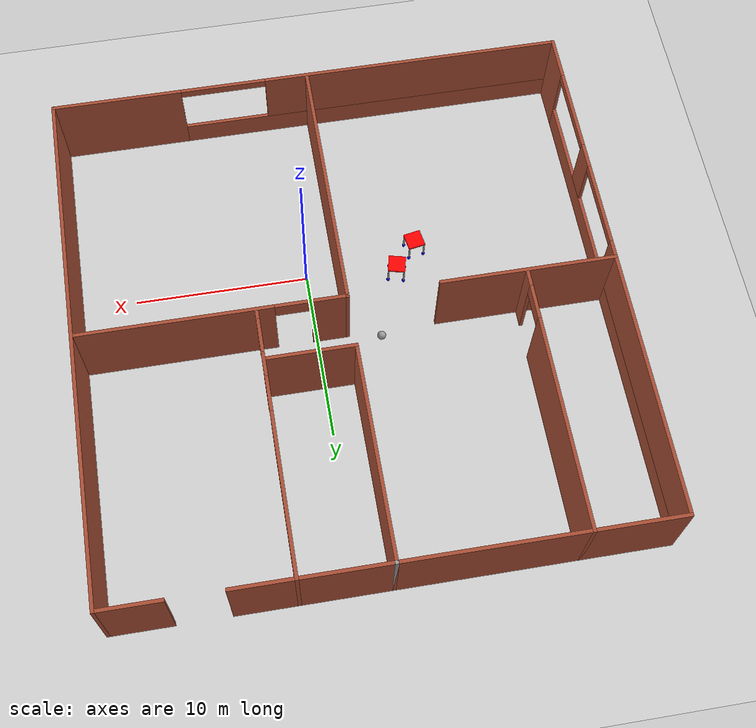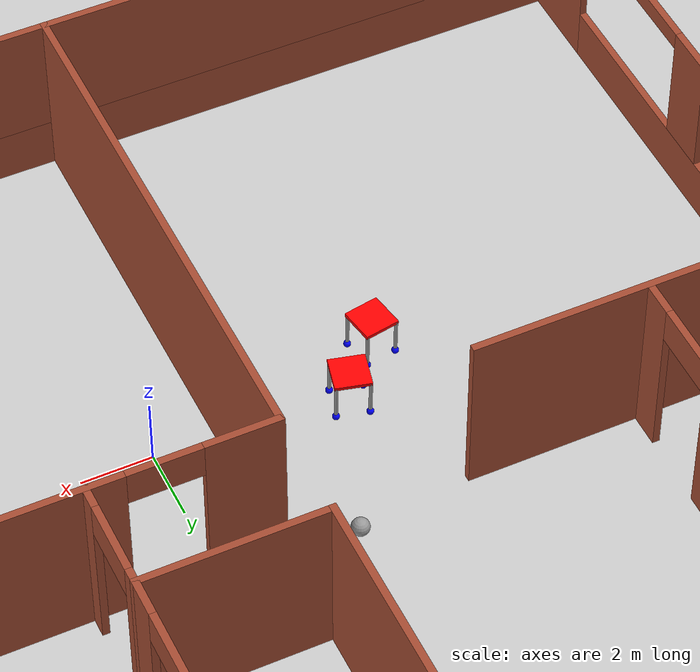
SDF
<sdf version="1.6">
 <world name="default">
  <model name="ground_plane">
   <static>1</static>
   <link name="link">
    <collision name="collision">
     <geometry><plane><normal>0 0 1</normal><size>100 100</size></plane></geometry>
     <surface><friction><ode><mu>100</mu><mu2>50</mu2></ode></friction></surface>
    </collision>
    <visual name="visual">
     <cast_shadows>0</cast_shadows>
     <geometry><plane><normal>0 0 1</normal><size>100 100</size></plane></geometry>
     <material>
      <script><uri>file://media/materials/scripts/gazebo.material</uri><name>Gazebo/Grey</name></script>
     </material>
    </visual>
   </link>
  </model>
  <gravity>0 0 -9.8</gravity>
  <magnetic_field>6e-06 2.3e-05 -4.2e-05</magnetic_field>
  <atmosphere type="adiabatic"/>
  <physics name="default_physics" default="0" type="ode">
   <max_step_size>0.001</max_step_size>
   <real_time_factor>1</real_time_factor>
   <real_time_update_rate>1000</real_time_update_rate>
  </physics>
  <scene><ambient>0.4 0.4 0.4 1</ambient><background>0.7 0.7 0.7 1</background><shadows>1</shadows></scene>
  <spherical_coordinates>
   <surface_model>EARTH_WGS84</surface_model>
   <latitude_deg>0</latitude_deg>
   <longitude_deg>0</longitude_deg>
   <elevation>0</elevation>
   <heading_deg>0</heading_deg>
  </spherical_coordinates>
  <model name="Appartment">
   <pose>-1.7896 4.0345 0 0 -0 0</pose>
   <link name="Door_1">
    <collision name="Door_1_Collision">
     <geometry><box><size>3 0.17 4</size></box></geometry>
     <pose>0 0 2 0 -0 0</pose>
    </collision>
    <visual name="Door_1_Visual">
     <pose>0 0 2 0 -0 0</pose>
     <geometry><box><size>3 0.17 4</size></box></geometry>
     <material>
      <script><uri>file://media/materials/scripts/gazebo.material</uri><name>Gazebo/Grey</name></script>
     </material>
    </visual>
    <pose>-10 -15 0 0 -0 0</pose>
   </link>
   <link name="Wall_26">
    <pose>-0.100001 15 0 0 -0 0</pose>
    <visual name="Wall_26_Visual_0">
     <pose>-3.2 0 2.5 0 -0 0</pose>
     <geometry><box><size>23.6 0.2 5</size></box></geometry>
     <material>
      <script><uri>file://media/materials/scripts/gazebo.material</uri><name>Gazebo/Bricks</name></script>
      <ambient>1 1 1 1</ambient>
     </material>
     <meta><layer>0</layer></meta>
    </visual>
    <collision name="Wall_26_Collision_0">
     <geometry><box><size>23.6 0.2 5</size></box></geometry>
     <pose>-3.2 0 2.5 0 -0 0</pose>
    </collision>
    <visual name="Wall_26_Visual_1">
     <pose>13.3 0 2.5 0 -0 0</pose>
     <geometry><box><size>3.4 0.2 5</size></box></geometry>
     <material>
      <script><uri>file://media/materials/scripts/gazebo.material</uri><name>Gazebo/Bricks</name></script>
      <ambient>1 1 1 1</ambient>
     </material>
     <meta><layer>0</layer></meta>
    </visual>
    <collision name="Wall_26_Collision_1">
     <geometry><box><size>3.4 0.2 5</size></box></geometry>
     <pose>13.3 0 2.5 0 -0 0</pose>
    </collision>
   </link>
   <link name="Wall_28">
    <collision name="Wall_28_Collision">
     <geometry><box><size>30.2 0.2 5</size></box></geometry>
     <pose>0 0 2.5 0 -0 0</pose>
    </collision>
    <visual name="Wall_28_Visual">
     <pose>0 0 2.5 0 -0 0</pose>
     <geometry><box><size>30.2 0.2 5</size></box></geometry>
     <material>
      <script><uri>file://media/materials/scripts/gazebo.material</uri><name>Gazebo/Bricks</name></script>
      <ambient>1 1 1 1</ambient>
     </material>
     <meta><layer>0</layer></meta>
    </visual>
    <pose>15 0 0 0 0 -1.5708</pose>
   </link>
   <link name="Wall_32">
    <pose>0.1 -15 0 0 -0 3.14159</pose>
    <visual name="Wall_32_Visual_0">
     <pose>-11.2 0 2.5 0 -0 0</pose>
     <geometry><box><size>7.6 0.2 5</size></box></geometry>
     <material>
      <script><uri>file://media/materials/scripts/gazebo.material</uri><name>Gazebo/Bricks</name></script>
      <ambient>1 1 1 1</ambient>
     </material>
     <meta><layer>0</layer></meta>
    </visual>
    <collision name="Wall_32_Collision_0">
     <geometry><box><size>7.6 0.2 5</size></box></geometry>
     <pose>-11.2 0 2.5 0 -0 0</pose>
    </collision>
    <visual name="Wall_32_Visual_1">
     <pose>3.8 0 0.75 0 -0 0</pose>
     <geometry><box><size>22.4 0.2 1.5</size></box></geometry>
     <material>
      <script><uri>file://media/materials/scripts/gazebo.material</uri><name>Gazebo/Bricks</name></script>
      <ambient>1 1 1 1</ambient>
     </material>
     <meta><layer>0</layer></meta>
    </visual>
    <collision name="Wall_32_Collision_1">
     <geometry><box><size>22.4 0.2 1.5</size></box></geometry>
     <pose>3.8 0 0.75 0 -0 0</pose>
    </collision>
    <visual name="Wall_32_Visual_2">
     <pose>6.3 0 3.25 0 -0 0</pose>
     <geometry><box><size>17.4 0.2 3.5</size></box></geometry>
     <material>
      <script><uri>file://media/materials/scripts/gazebo.material</uri><name>Gazebo/Bricks</name></script>
      <ambient>1 1 1 1</ambient>
     </material>
     <meta><layer>0</layer></meta>
    </visual>
    <collision name="Wall_32_Collision_2">
     <geometry><box><size>17.4 0.2 3.5</size></box></geometry>
     <pose>6.3 0 3.25 0 -0 0</pose>
    </collision>
    <visual name="Wall_32_Visual_3">
     <pose>-4.9 0 4.75 0 -0 0</pose>
     <geometry><box><size>5 0.2 0.5</size></box></geometry>
     <material>
      <script><uri>file://media/materials/scripts/gazebo.material</uri><name>Gazebo/Bricks</name></script>
      <ambient>1 1 1 1</ambient>
     </material>
     <meta><layer>0</layer></meta>
    </visual>
    <collision name="Wall_32_Collision_3">
     <geometry><box><size>5 0.2 0.5</size></box></geometry>
     <pose>-4.9 0 4.75 0 -0 0</pose>
    </collision>
   </link>
   <link name="Wall_37">
    <pose>-15 -0.1 0 0 -0 1.5708</pose>
    <visual name="Wall_37_Visual_0">
     <pose>-13.7 0 2.5 0 -0 0</pose>
     <geometry><box><size>2.6 0.2 5</size></box></geometry>
     <material>
      <script><uri>file://media/materials/scripts/gazebo.material</uri><name>Gazebo/Bricks</name></script>
      <ambient>1 1 1 1</ambient>
     </material>
     <meta><layer>0</layer></meta>
    </visual>
    <collision name="Wall_37_Collision_0">
     <geometry><box><size>2.6 0.2 5</size></box></geometry>
     <pose>-13.7 0 2.5 0 -0 0</pose>
    </collision>
    <visual name="Wall_37_Visual_1">
     <pose>1.3 0 0.75 0 -0 0</pose>
     <geometry><box><size>27.4 0.2 1.5</size></box></geometry>
     <material>
      <script><uri>file://media/materials/scripts/gazebo.material</uri><name>Gazebo/Bricks</name></script>
      <ambient>1 1 1 1</ambient>
     </material>
     <meta><layer>0</layer></meta>
    </visual>
    <collision name="Wall_37_Collision_1">
     <geometry><box><size>27.4 0.2 1.5</size></box></geometry>
     <pose>1.3 0 0.75 0 -0 0</pose>
    </collision>
    <visual name="Wall_37_Visual_2">
     <pose>-6.65 0 3.25 0 -0 0</pose>
     <geometry><box><size>1.5 0.2 3.5</size></box></geometry>
     <material>
      <script><uri>file://media/materials/scripts/gazebo.material</uri><name>Gazebo/Bricks</name></script>
      <ambient>1 1 1 1</ambient>
     </material>
     <meta><layer>0</layer></meta>
    </visual>
    <collision name="Wall_37_Collision_2">
     <geometry><box><size>1.5 0.2 3.5</size></box></geometry>
     <pose>-6.65 0 3.25 0 -0 0</pose>
    </collision>
    <visual name="Wall_37_Visual_3">
     <pose>7.05 0 3.25 0 -0 0</pose>
     <geometry><box><size>15.9 0.2 3.5</size></box></geometry>
     <material>
      <script><uri>file://media/materials/scripts/gazebo.material</uri><name>Gazebo/Bricks</name></script>
      <ambient>1 1 1 1</ambient>
     </material>
     <meta><layer>0</layer></meta>
    </visual>
    <collision name="Wall_37_Collision_3">
     <geometry><box><size>15.9 0.2 3.5</size></box></geometry>
     <pose>7.05 0 3.25 0 -0 0</pose>
    </collision>
    <visual name="Wall_37_Visual_4">
     <pose>-9.9 0 4.75 0 -0 0</pose>
     <geometry><box><size>5 0.2 0.5</size></box></geometry>
     <material>
      <script><uri>file://media/materials/scripts/gazebo.material</uri><name>Gazebo/Bricks</name></script>
      <ambient>1 1 1 1</ambient>
     </material>
     <meta><layer>0</layer></meta>
    </visual>
    <collision name="Wall_37_Collision_4">
     <geometry><box><size>5 0.2 0.5</size></box></geometry>
     <pose>-9.9 0 4.75 0 -0 0</pose>
    </collision>
    <visual name="Wall_37_Visual_5">
     <pose>-3.4 0 4.75 0 -0 0</pose>
     <geometry><box><size>5 0.2 0.5</size></box></geometry>
     <material>
      <script><uri>file://media/materials/scripts/gazebo.material</uri><name>Gazebo/Bricks</name></script>
      <ambient>1 1 1 1</ambient>
     </material>
     <meta><layer>0</layer></meta>
    </visual>
    <collision name="Wall_37_Collision_5">
     <geometry><box><size>5 0.2 0.5</size></box></geometry>
     <pose>-3.4 0 4.75 0 -0 0</pose>
    </collision>
   </link>
   <link name="Wall_39">
    <collision name="Wall_39_Collision">
     <geometry><box><size>0.2 0.2 5</size></box></geometry>
     <pose>0 0 2.5 0 -0 0</pose>
    </collision>
    <visual name="Wall_39_Visual">
     <pose>0 0 2.5 0 -0 0</pose>
     <geometry><box><size>0.2 0.2 5</size></box></geometry>
     <material>
      <script><uri>file://media/materials/scripts/gazebo.material</uri><name>Gazebo/Grey</name></script>
      <ambient>1 1 1 1</ambient>
     </material>
     <meta><layer>0</layer></meta>
    </visual>
    <pose>0 15 0 0 -0 0</pose>
   </link>
   <link name="Wall_42">
    <collision name="Wall_42_Collision">
     <geometry><box><size>12.2 0.2 5</size></box></geometry>
     <pose>0 0 2.5 0 -0 0</pose>
    </collision>
    <visual name="Wall_42_Visual">
     <pose>0 0 2.5 0 -0 0</pose>
     <geometry><box><size>12.2 0.2 5</size></box></geometry>
     <material>
      <script><uri>file://media/materials/scripts/gazebo.material</uri><name>Gazebo/Bricks</name></script>
      <ambient>1 1 1 1</ambient>
     </material>
     <meta><layer>0</layer></meta>
    </visual>
    <pose>0 9 0 0 0 -1.5708</pose>
   </link>
   <link name="Wall_46">
    <collision name="Wall_46_Collision">
     <geometry><box><size>10 0.2 5</size></box></geometry>
     <pose>0 0 2.5 0 -0 0</pose>
    </collision>
    <visual name="Wall_46_Visual">
     <pose>0 0 2.5 0 -0 0</pose>
     <geometry><box><size>10 0.2 5</size></box></geometry>
     <material>
      <script><uri>file://media/materials/scripts/gazebo.material</uri><name>Gazebo/Bricks</name></script>
      <ambient>1 1 1 1</ambient>
     </material>
     <meta><layer>0</layer></meta>
    </visual>
    <pose>-10.1 0 0 0 -0 0</pose>
   </link>
   <link name="Wall_49">
    <pose>-10 7.6 0 0 0 -1.5708</pose>
    <visual name="Wall_49_Visual_0">
     <pose>-1.45 0 2.5 0 -0 0</pose>
     <geometry><box><size>12.1 0.2 5</size></box></geometry>
     <material>
      <script><uri>file://media/materials/scripts/gazebo.material</uri><name>Gazebo/Bricks</name></script>
      <ambient>1 1 1 1</ambient>
     </material>
     <meta><layer>0</layer></meta>
    </visual>
    <collision name="Wall_49_Collision_0">
     <geometry><box><size>12.1 0.2 5</size></box></geometry>
     <pose>-1.45 0 2.5 0 -0 0</pose>
    </collision>
    <visual name="Wall_49_Visual_1">
     <pose>7.05 0 2.5 0 -0 0</pose>
     <geometry><box><size>0.9 0.2 5</size></box></geometry>
     <material>
      <script><uri>file://media/materials/scripts/gazebo.material</uri><name>Gazebo/Bricks</name></script>
      <ambient>1 1 1 1</ambient>
     </material>
     <meta><layer>0</layer></meta>
    </visual>
    <collision name="Wall_49_Collision_1">
     <geometry><box><size>0.9 0.2 5</size></box></geometry>
     <pose>7.05 0 2.5 0 -0 0</pose>
    </collision>
    <visual name="Wall_49_Visual_2">
     <pose>5.6 0 4.5 0 -0 0</pose>
     <geometry><box><size>2 0.2 1</size></box></geometry>
     <material>
      <script><uri>file://media/materials/scripts/gazebo.material</uri><name>Gazebo/Bricks</name></script>
      <ambient>1 1 1 1</ambient>
     </material>
     <meta><layer>0</layer></meta>
    </visual>
    <collision name="Wall_49_Collision_2">
     <geometry><box><size>2 0.2 1</size></box></geometry>
     <pose>5.6 0 4.5 0 -0 0</pose>
    </collision>
   </link>
   <link name="Wall_51">
    <pose>5 7.5 0 0 0 -1.5708</pose>
    <visual name="Wall_51_Visual_0">
     <pose>-3.05 0 2.5 0 -0 0</pose>
     <geometry><box><size>9.1 0.2 5</size></box></geometry>
     <material>
      <script><uri>file://media/materials/scripts/gazebo.material</uri><name>Gazebo/Bricks</name></script>
      <ambient>1 1 1 1</ambient>
     </material>
     <meta><layer>0</layer></meta>
    </visual>
    <collision name="Wall_51_Collision_0">
     <geometry><box><size>9.1 0.2 5</size></box></geometry>
     <pose>-3.05 0 2.5 0 -0 0</pose>
    </collision>
    <visual name="Wall_51_Visual_1">
     <pose>4.20298 0 2.5 0 -0 0</pose>
     <geometry><box><size>1.40597 0.2 5</size></box></geometry>
     <material>
      <script><uri>file://media/materials/scripts/gazebo.material</uri><name>Gazebo/Bricks</name></script>
      <ambient>1 1 1 1</ambient>
     </material>
     <meta><layer>0</layer></meta>
    </visual>
    <collision name="Wall_51_Collision_1">
     <geometry><box><size>1.40597 0.2 5</size></box></geometry>
     <pose>4.20298 0 2.5 0 -0 0</pose>
    </collision>
    <visual name="Wall_51_Visual_2">
     <pose>7.25298 0 2.5 0 -0 0</pose>
     <geometry><box><size>0.694034 0.2 5</size></box></geometry>
     <material>
      <script><uri>file://media/materials/scripts/gazebo.material</uri><name>Gazebo/Bricks</name></script>
      <ambient>1 1 1 1</ambient>
     </material>
     <meta><layer>0</layer></meta>
    </visual>
    <collision name="Wall_51_Collision_2">
     <geometry><box><size>0.694034 0.2 5</size></box></geometry>
     <pose>7.25298 0 2.5 0 -0 0</pose>
    </collision>
    <visual name="Wall_51_Visual_3">
     <pose>2.5 0 4.5 0 -0 0</pose>
     <geometry><box><size>2 0.2 1</size></box></geometry>
     <material>
      <script><uri>file://media/materials/scripts/gazebo.material</uri><name>Gazebo/Bricks</name></script>
      <ambient>1 1 1 1</ambient>
     </material>
     <meta><layer>0</layer></meta>
    </visual>
    <collision name="Wall_51_Collision_3">
     <geometry><box><size>2 0.2 1</size></box></geometry>
     <pose>2.5 0 4.5 0 -0 0</pose>
    </collision>
    <visual name="Wall_51_Visual_4">
     <pose>5.90597 0 4.5 0 -0 0</pose>
     <geometry><box><size>2 0.2 1</size></box></geometry>
     <material>
      <script><uri>file://media/materials/scripts/gazebo.material</uri><name>Gazebo/Bricks</name></script>
      <ambient>1 1 1 1</ambient>
     </material>
     <meta><layer>0</layer></meta>
    </visual>
    <collision name="Wall_51_Collision_4">
     <geometry><box><size>2 0.2 1</size></box></geometry>
     <pose>5.90597 0 4.5 0 -0 0</pose>
    </collision>
   </link>
   <link name="Wall_55">
    <collision name="Wall_55_Collision">
     <geometry><box><size>15.2 0.2 5</size></box></geometry>
     <pose>0 0 2.5 0 -0 0</pose>
    </collision>
    <visual name="Wall_55_Visual">
     <pose>0 0 2.5 0 -0 0</pose>
     <geometry><box><size>15.2 0.2 5</size></box></geometry>
     <material>
      <script><uri>file://media/materials/scripts/gazebo.material</uri><name>Gazebo/Bricks</name></script>
      <ambient>1 1 1 1</ambient>
     </material>
     <meta><layer>0</layer></meta>
    </visual>
    <pose>0 -7.5 0 0 -0 1.5708</pose>
   </link>
   <link name="Wall_57">
    <pose>7.5 0 0 0 -0 0</pose>
    <visual name="Wall_57_Visual_0">
     <pose>-6.55 0 2.5 0 -0 0</pose>
     <geometry><box><size>2.1 0.2 5</size></box></geometry>
     <material>
      <script><uri>file://media/materials/scripts/gazebo.material</uri><name>Gazebo/Bricks</name></script>
      <ambient>1 1 1 1</ambient>
     </material>
     <meta><layer>0</layer></meta>
    </visual>
    <collision name="Wall_57_Collision_0">
     <geometry><box><size>2.1 0.2 5</size></box></geometry>
     <pose>-6.55 0 2.5 0 -0 0</pose>
    </collision>
    <visual name="Wall_57_Visual_1">
     <pose>2.05 0 2.5 0 -0 0</pose>
     <geometry><box><size>11.1 0.2 5</size></box></geometry>
     <material>
      <script><uri>file://media/materials/scripts/gazebo.material</uri><name>Gazebo/Bricks</name></script>
      <ambient>1 1 1 1</ambient>
     </material>
     <meta><layer>0</layer></meta>
    </visual>
    <collision name="Wall_57_Collision_1">
     <geometry><box><size>11.1 0.2 5</size></box></geometry>
     <pose>2.05 0 2.5 0 -0 0</pose>
    </collision>
    <visual name="Wall_57_Visual_2">
     <pose>-4.5 0 4.5 0 -0 0</pose>
     <geometry><box><size>2 0.2 1</size></box></geometry>
     <material>
      <script><uri>file://media/materials/scripts/gazebo.material</uri><name>Gazebo/Bricks</name></script>
      <ambient>1 1 1 1</ambient>
     </material>
     <meta><layer>0</layer></meta>
    </visual>
    <collision name="Wall_57_Collision_2">
     <geometry><box><size>2 0.2 1</size></box></geometry>
     <pose>-4.5 0 4.5 0 -0 0</pose>
    </collision>
   </link>
   <link name="Wall_61">
    <collision name="Wall_61_Collision">
     <geometry><box><size>5.2 0.2 5</size></box></geometry>
     <pose>0 0 2.5 0 -0 0</pose>
    </collision>
    <visual name="Wall_61_Visual">
     <pose>0 0 2.5 0 -0 0</pose>
     <geometry><box><size>5.2 0.2 5</size></box></geometry>
     <material>
      <script><uri>file://media/materials/scripts/gazebo.material</uri><name>Gazebo/Bricks</name></script>
      <ambient>1 1 1 1</ambient>
     </material>
     <meta><layer>0</layer></meta>
    </visual>
    <pose>2.5 3 0 0 -0 0</pose>
   </link>
   <static>1</static>
  </model>
  <model name="Robo_Model_3">
   <link name="link_0">
    <pose>-0.003409 0.00263 0.716269 0 -0 0</pose>
    <inertial>
     <mass>1</mass>
     <inertia>
      <ixx>0.166667</ixx>
      <ixy>0</ixy>
      <ixz>0</ixz>
      <iyy>0.166667</iyy>
      <iyz>0</iyz>
      <izz>0.166667</izz>
     </inertia>
    </inertial>
    <visual name="visual">
     <geometry><box><size>1 1 0.1</size></box></geometry>
     <material>
      <lighting>1</lighting>
      <script><uri>file://media/materials/scripts/gazebo.material</uri><name>Gazebo/Grey</name></script>
      <shader type="pixel"><normal_map>__default__</normal_map></shader>
      <ambient>1 0 0 1</ambient>
      <diffuse>0.7 0.7 0.7 1</diffuse>
      <specular>0.01 0.01 0.01 1</specular>
      <emissive>0 0 0 1</emissive>
     </material>
    </visual>
    <collision name="collision">
     <geometry><box><size>1 1 0.1</size></box></geometry>
     <surface>
      <friction>
       <ode><mu>1</mu><mu2>1</mu2><fdir1>0 0 0</fdir1><slip1>0</slip1><slip2>0</slip2></ode>
       <torsional>
        <coefficient>1</coefficient>
        <patch_radius>0</patch_radius>
        <surface_radius>0</surface_radius>
        <use_patch_radius>1</use_patch_radius>
        <ode><slip>0</slip></ode>
       </torsional>
      </friction>
      <bounce><restitution_coefficient>0</restitution_coefficient><threshold>1e+06</threshold></bounce>
      <contact>
       <collide_without_contact>0</collide_without_contact>
       <collide_without_contact_bitmask>1</collide_without_contact_bitmask>
       <collide_bitmask>1</collide_bitmask>
       <ode>
        <soft_cfm>0</soft_cfm>
        <soft_erp>0.2</soft_erp>
        <kp>1e+13</kp>
        <kd>1</kd>
        <max_vel>0.01</max_vel>
        <min_depth>0</min_depth>
       </ode>
       <bullet>
        <split_impulse>1</split_impulse>
        <split_impulse_penetration_threshold>-0.01</split_impulse_penetration_threshold>
        <soft_cfm>0</soft_cfm>
        <soft_erp>0.2</soft_erp>
        <kp>1e+13</kp>
        <kd>1</kd>
       </bullet>
      </contact>
     </surface>
    </collision>
   </link>
   <link name="link_1">
    <pose>0.450427 -0.450329 0.216269 0 -0 0</pose>
    <inertial>
     <mass>1</mass>
     <inertia><ixx>0.145833</ixx><ixy>0</ixy><ixz>0</ixz><iyy>0.145833</iyy><iyz>0</iyz><izz>0.125</izz></inertia>
    </inertial>
    <visual name="visual">
     <geometry><cylinder><radius>0.05</radius><length>1</length></cylinder></geometry>
     <material>
      <lighting>1</lighting>
      <script><uri>file://media/materials/scripts/gazebo.material</uri><name>Gazebo/Grey</name></script>
      <shader type="pixel"><normal_map>__default__</normal_map></shader>
      <ambient>0.3 0.3 0.3 1</ambient>
      <diffuse>0.7 0.7 0.7 1</diffuse>
      <specular>0.01 0.01 0.01 1</specular>
      <emissive>0 0 0 1</emissive>
     </material>
    </visual>
    <collision name="collision">
     <geometry><cylinder><radius>0.05</radius><length>1</length></cylinder></geometry>
     <surface>
      <friction>
       <ode><mu>1</mu><mu2>1</mu2><fdir1>0 0 0</fdir1><slip1>0</slip1><slip2>0</slip2></ode>
       <torsional>
        <coefficient>1</coefficient>
        <patch_radius>0</patch_radius>
        <surface_radius>0</surface_radius>
        <use_patch_radius>1</use_patch_radius>
        <ode><slip>0</slip></ode>
       </torsional>
      </friction>
      <bounce><restitution_coefficient>0</restitution_coefficient><threshold>1e+06</threshold></bounce>
      <contact>
       <collide_without_contact>0</collide_without_contact>
       <collide_without_contact_bitmask>1</collide_without_contact_bitmask>
       <collide_bitmask>1</collide_bitmask>
       <ode>
        <soft_cfm>0</soft_cfm>
        <soft_erp>0.2</soft_erp>
        <kp>1e+13</kp>
        <kd>1</kd>
        <max_vel>0.01</max_vel>
        <min_depth>0</min_depth>
       </ode>
       <bullet>
        <split_impulse>1</split_impulse>
        <split_impulse_penetration_threshold>-0.01</split_impulse_penetration_threshold>
        <soft_cfm>0</soft_cfm>
        <soft_erp>0.2</soft_erp>
        <kp>1e+13</kp>
        <kd>1</kd>
       </bullet>
      </contact>
     </surface>
    </collision>
   </link>
   <link name="link_1_clone">
    <pose>-0.449573 -0.450329 0.208531 0 -0 0</pose>
    <inertial>
     <mass>1</mass>
     <inertia><ixx>0.145833</ixx><ixy>0</ixy><ixz>0</ixz><iyy>0.145833</iyy><iyz>0</iyz><izz>0.125</izz></inertia>
    </inertial>
    <visual name="visual">
     <geometry><cylinder><radius>0.05</radius><length>1</length></cylinder></geometry>
     <material>
      <lighting>1</lighting>
      <script><uri>file://media/materials/scripts/gazebo.material</uri><name>Gazebo/Grey</name></script>
      <shader type="pixel"><normal_map>__default__</normal_map></shader>
      <ambient>0.3 0.3 0.3 1</ambient>
      <diffuse>0.7 0.7 0.7 1</diffuse>
      <specular>0.01 0.01 0.01 1</specular>
      <emissive>0 0 0 1</emissive>
     </material>
    </visual>
    <collision name="collision">
     <geometry><cylinder><radius>0.05</radius><length>1</length></cylinder></geometry>
     <surface>
      <friction>
       <ode><mu>1</mu><mu2>1</mu2><fdir1>0 0 0</fdir1><slip1>0</slip1><slip2>0</slip2></ode>
       <torsional>
        <coefficient>1</coefficient>
        <patch_radius>0</patch_radius>
        <surface_radius>0</surface_radius>
        <use_patch_radius>1</use_patch_radius>
        <ode><slip>0</slip></ode>
       </torsional>
      </friction>
      <bounce><restitution_coefficient>0</restitution_coefficient><threshold>1e+06</threshold></bounce>
      <contact>
       <collide_without_contact>0</collide_without_contact>
       <collide_without_contact_bitmask>1</collide_without_contact_bitmask>
       <collide_bitmask>1</collide_bitmask>
       <ode>
        <soft_cfm>0</soft_cfm>
        <soft_erp>0.2</soft_erp>
        <kp>1e+13</kp>
        <kd>1</kd>
        <max_vel>0.01</max_vel>
        <min_depth>0</min_depth>
       </ode>
       <bullet>
        <split_impulse>1</split_impulse>
        <split_impulse_penetration_threshold>-0.01</split_impulse_penetration_threshold>
        <soft_cfm>0</soft_cfm>
        <soft_erp>0.2</soft_erp>
        <kp>1e+13</kp>
        <kd>1</kd>
       </bullet>
      </contact>
     </surface>
    </collision>
   </link>
   <link name="link_1_clone_clone">
    <pose>-0.449573 0.449671 0.208532 0 -0 0</pose>
    <inertial>
     <mass>1</mass>
     <inertia><ixx>0.145833</ixx><ixy>0</ixy><ixz>0</ixz><iyy>0.145833</iyy><iyz>0</iyz><izz>0.125</izz></inertia>
    </inertial>
    <visual name="visual">
     <geometry><cylinder><radius>0.05</radius><length>1</length></cylinder></geometry>
     <material>
      <lighting>1</lighting>
      <script><uri>file://media/materials/scripts/gazebo.material</uri><name>Gazebo/Grey</name></script>
      <shader type="pixel"><normal_map>__default__</normal_map></shader>
      <ambient>0.3 0.3 0.3 1</ambient>
      <diffuse>0.7 0.7 0.7 1</diffuse>
      <specular>0.01 0.01 0.01 1</specular>
      <emissive>0 0 0 1</emissive>
     </material>
    </visual>
    <collision name="collision">
     <geometry><cylinder><radius>0.05</radius><length>1</length></cylinder></geometry>
     <surface>
      <friction>
       <ode><mu>1</mu><mu2>1</mu2><fdir1>0 0 0</fdir1><slip1>0</slip1><slip2>0</slip2></ode>
       <torsional>
        <coefficient>1</coefficient>
        <patch_radius>0</patch_radius>
        <surface_radius>0</surface_radius>
        <use_patch_radius>1</use_patch_radius>
        <ode><slip>0</slip></ode>
       </torsional>
      </friction>
      <bounce><restitution_coefficient>0</restitution_coefficient><threshold>1e+06</threshold></bounce>
      <contact>
       <collide_without_contact>0</collide_without_contact>
       <collide_without_contact_bitmask>1</collide_without_contact_bitmask>
       <collide_bitmask>1</collide_bitmask>
       <ode>
        <soft_cfm>0</soft_cfm>
        <soft_erp>0.2</soft_erp>
        <kp>1e+13</kp>
        <kd>1</kd>
        <max_vel>0.01</max_vel>
        <min_depth>0</min_depth>
       </ode>
       <bullet>
        <split_impulse>1</split_impulse>
        <split_impulse_penetration_threshold>-0.01</split_impulse_penetration_threshold>
        <soft_cfm>0</soft_cfm>
        <soft_erp>0.2</soft_erp>
        <kp>1e+13</kp>
        <kd>1</kd>
       </bullet>
      </contact>
     </surface>
    </collision>
   </link>
   <link name="link_1_clone_clone_clone">
    <pose>0.450427 0.449671 0.208532 0 -0 0</pose>
    <inertial>
     <mass>1</mass>
     <inertia><ixx>0.145833</ixx><ixy>0</ixy><ixz>0</ixz><iyy>0.145833</iyy><iyz>0</iyz><izz>0.125</izz></inertia>
    </inertial>
    <visual name="visual">
     <geometry><cylinder><radius>0.05</radius><length>1</length></cylinder></geometry>
     <material>
      <lighting>1</lighting>
      <script><uri>file://media/materials/scripts/gazebo.material</uri><name>Gazebo/Grey</name></script>
      <shader type="pixel"><normal_map>__default__</normal_map></shader>
      <ambient>0.3 0.3 0.3 1</ambient>
      <diffuse>0.7 0.7 0.7 1</diffuse>
      <specular>0.01 0.01 0.01 1</specular>
      <emissive>0 0 0 1</emissive>
     </material>
    </visual>
    <collision name="collision">
     <geometry><cylinder><radius>0.05</radius><length>1</length></cylinder></geometry>
     <surface>
      <friction>
       <ode><mu>1</mu><mu2>1</mu2><fdir1>0 0 0</fdir1><slip1>0</slip1><slip2>0</slip2></ode>
       <torsional>
        <coefficient>1</coefficient>
        <patch_radius>0</patch_radius>
        <surface_radius>0</surface_radius>
        <use_patch_radius>1</use_patch_radius>
        <ode><slip>0</slip></ode>
       </torsional>
      </friction>
      <bounce><restitution_coefficient>0</restitution_coefficient><threshold>1e+06</threshold></bounce>
      <contact>
       <collide_without_contact>0</collide_without_contact>
       <collide_without_contact_bitmask>1</collide_without_contact_bitmask>
       <collide_bitmask>1</collide_bitmask>
       <ode>
        <soft_cfm>0</soft_cfm>
        <soft_erp>0.2</soft_erp>
        <kp>1e+13</kp>
        <kd>1</kd>
        <max_vel>0.01</max_vel>
        <min_depth>0</min_depth>
       </ode>
       <bullet>
        <split_impulse>1</split_impulse>
        <split_impulse_penetration_threshold>-0.01</split_impulse_penetration_threshold>
        <soft_cfm>0</soft_cfm>
        <soft_erp>0.2</soft_erp>
        <kp>1e+13</kp>
        <kd>1</kd>
       </bullet>
      </contact>
     </surface>
    </collision>
   </link>
   <link name="link_2">
    <pose>0.450427 -0.450329 -0.383731 0 -0 0</pose>
    <inertial>
     <mass>1</mass>
     <inertia><ixx>0.1</ixx><ixy>0</ixy><ixz>0</ixz><iyy>0.1</iyy><iyz>0</iyz><izz>0.1</izz></inertia>
    </inertial>
    <visual name="visual">
     <geometry><sphere><radius>0.1</radius></sphere></geometry>
     <material>
      <lighting>1</lighting>
      <script><uri>file://media/materials/scripts/gazebo.material</uri><name>Gazebo/Grey</name></script>
      <shader type="pixel"><normal_map>__default__</normal_map></shader>
      <ambient>0 0 1 1</ambient>
      <diffuse>0.7 0.7 0.7 1</diffuse>
      <specular>0.01 0.01 0.01 1</specular>
      <emissive>0 0 0 1</emissive>
     </material>
    </visual>
    <collision name="collision">
     <geometry><sphere><radius>0.1</radius></sphere></geometry>
     <surface>
      <friction>
       <ode><mu>1</mu><mu2>1</mu2><fdir1>0 0 0</fdir1><slip1>0</slip1><slip2>0</slip2></ode>
       <torsional>
        <coefficient>1</coefficient>
        <patch_radius>0</patch_radius>
        <surface_radius>0</surface_radius>
        <use_patch_radius>1</use_patch_radius>
        <ode><slip>0</slip></ode>
       </torsional>
      </friction>
      <bounce><restitution_coefficient>0</restitution_coefficient><threshold>1e+06</threshold></bounce>
      <contact>
       <collide_without_contact>0</collide_without_contact>
       <collide_without_contact_bitmask>1</collide_without_contact_bitmask>
       <collide_bitmask>1</collide_bitmask>
       <ode>
        <soft_cfm>0</soft_cfm>
        <soft_erp>0.2</soft_erp>
        <kp>1e+13</kp>
        <kd>1</kd>
        <max_vel>0.01</max_vel>
        <min_depth>0</min_depth>
       </ode>
       <bullet>
        <split_impulse>1</split_impulse>
        <split_impulse_penetration_threshold>-0.01</split_impulse_penetration_threshold>
        <soft_cfm>0</soft_cfm>
        <soft_erp>0.2</soft_erp>
        <kp>1e+13</kp>
        <kd>1</kd>
       </bullet>
      </contact>
     </surface>
    </collision>
   </link>
   <link name="link_2_clone">
    <pose>0.450427 0.449671 -0.391468 0 -0 0</pose>
    <inertial>
     <mass>1</mass>
     <inertia><ixx>0.1</ixx><ixy>0</ixy><ixz>0</ixz><iyy>0.1</iyy><iyz>0</iyz><izz>0.1</izz></inertia>
    </inertial>
    <visual name="visual">
     <geometry><sphere><radius>0.1</radius></sphere></geometry>
     <material>
      <lighting>1</lighting>
      <script><uri>file://media/materials/scripts/gazebo.material</uri><name>Gazebo/Grey</name></script>
      <shader type="pixel"><normal_map>__default__</normal_map></shader>
      <ambient>0 0 1 1</ambient>
      <diffuse>0.7 0.7 0.7 1</diffuse>
      <specular>0.01 0.01 0.01 1</specular>
      <emissive>0 0 0 1</emissive>
     </material>
    </visual>
    <collision name="collision">
     <geometry><sphere><radius>0.1</radius></sphere></geometry>
     <surface>
      <friction>
       <ode><mu>1</mu><mu2>1</mu2><fdir1>0 0 0</fdir1><slip1>0</slip1><slip2>0</slip2></ode>
       <torsional>
        <coefficient>1</coefficient>
        <patch_radius>0</patch_radius>
        <surface_radius>0</surface_radius>
        <use_patch_radius>1</use_patch_radius>
        <ode><slip>0</slip></ode>
       </torsional>
      </friction>
      <bounce><restitution_coefficient>0</restitution_coefficient><threshold>1e+06</threshold></bounce>
      <contact>
       <collide_without_contact>0</collide_without_contact>
       <collide_without_contact_bitmask>1</collide_without_contact_bitmask>
       <collide_bitmask>1</collide_bitmask>
       <ode>
        <soft_cfm>0</soft_cfm>
        <soft_erp>0.2</soft_erp>
        <kp>1e+13</kp>
        <kd>1</kd>
        <max_vel>0.01</max_vel>
        <min_depth>0</min_depth>
       </ode>
       <bullet>
        <split_impulse>1</split_impulse>
        <split_impulse_penetration_threshold>-0.01</split_impulse_penetration_threshold>
        <soft_cfm>0</soft_cfm>
        <soft_erp>0.2</soft_erp>
        <kp>1e+13</kp>
        <kd>1</kd>
       </bullet>
      </contact>
     </surface>
    </collision>
   </link>
   <link name="link_2_clone_clone">
    <pose>-0.449573 0.449671 -0.391468 0 -0 0</pose>
    <inertial>
     <mass>1</mass>
     <inertia><ixx>0.1</ixx><ixy>0</ixy><ixz>0</ixz><iyy>0.1</iyy><iyz>0</iyz><izz>0.1</izz></inertia>
    </inertial>
    <visual name="visual">
     <geometry><sphere><radius>0.1</radius></sphere></geometry>
     <material>
      <lighting>1</lighting>
      <script><uri>file://media/materials/scripts/gazebo.material</uri><name>Gazebo/Grey</name></script>
      <shader type="pixel"><normal_map>__default__</normal_map></shader>
      <ambient>0 0 1 1</ambient>
      <diffuse>0.7 0.7 0.7 1</diffuse>
      <specular>0.01 0.01 0.01 1</specular>
      <emissive>0 0 0 1</emissive>
     </material>
    </visual>
    <collision name="collision">
     <geometry><sphere><radius>0.1</radius></sphere></geometry>
     <surface>
      <friction>
       <ode><mu>1</mu><mu2>1</mu2><fdir1>0 0 0</fdir1><slip1>0</slip1><slip2>0</slip2></ode>
       <torsional>
        <coefficient>1</coefficient>
        <patch_radius>0</patch_radius>
        <surface_radius>0</surface_radius>
        <use_patch_radius>1</use_patch_radius>
        <ode><slip>0</slip></ode>
       </torsional>
      </friction>
      <bounce><restitution_coefficient>0</restitution_coefficient><threshold>1e+06</threshold></bounce>
      <contact>
       <collide_without_contact>0</collide_without_contact>
       <collide_without_contact_bitmask>1</collide_without_contact_bitmask>
       <collide_bitmask>1</collide_bitmask>
       <ode>
        <soft_cfm>0</soft_cfm>
        <soft_erp>0.2</soft_erp>
        <kp>1e+13</kp>
        <kd>1</kd>
        <max_vel>0.01</max_vel>
        <min_depth>0</min_depth>
       </ode>
       <bullet>
        <split_impulse>1</split_impulse>
        <split_impulse_penetration_threshold>-0.01</split_impulse_penetration_threshold>
        <soft_cfm>0</soft_cfm>
        <soft_erp>0.2</soft_erp>
        <kp>1e+13</kp>
        <kd>1</kd>
       </bullet>
      </contact>
     </surface>
    </collision>
   </link>
   <link name="link_2_clone_clone_clone">
    <pose>-0.449573 -0.450329 -0.391469 0 -0 0</pose>
    <inertial>
     <mass>1</mass>
     <inertia><ixx>0.1</ixx><ixy>0</ixy><ixz>0</ixz><iyy>0.1</iyy><iyz>0</iyz><izz>0.1</izz></inertia>
    </inertial>
    <visual name="visual">
     <geometry><sphere><radius>0.1</radius></sphere></geometry>
     <material>
      <lighting>1</lighting>
      <script><uri>file://media/materials/scripts/gazebo.material</uri><name>Gazebo/Grey</name></script>
      <shader type="pixel"><normal_map>__default__</normal_map></shader>
      <ambient>0 0 1 1</ambient>
      <diffuse>0.7 0.7 0.7 1</diffuse>
      <specular>0.01 0.01 0.01 1</specular>
      <emissive>0 0 0 1</emissive>
     </material>
    </visual>
    <collision name="collision">
     <geometry><sphere><radius>0.1</radius></sphere></geometry>
     <surface>
      <friction>
       <ode><mu>1</mu><mu2>1</mu2><fdir1>0 0 0</fdir1><slip1>0</slip1><slip2>0</slip2></ode>
       <torsional>
        <coefficient>1</coefficient>
        <patch_radius>0</patch_radius>
        <surface_radius>0</surface_radius>
        <use_patch_radius>1</use_patch_radius>
        <ode><slip>0</slip></ode>
       </torsional>
      </friction>
      <bounce><restitution_coefficient>0</restitution_coefficient><threshold>1e+06</threshold></bounce>
      <contact>
       <collide_without_contact>0</collide_without_contact>
       <collide_without_contact_bitmask>1</collide_without_contact_bitmask>
       <collide_bitmask>1</collide_bitmask>
       <ode>
        <soft_cfm>0</soft_cfm>
        <soft_erp>0.2</soft_erp>
        <kp>1e+13</kp>
        <kd>1</kd>
        <max_vel>0.01</max_vel>
        <min_depth>0</min_depth>
       </ode>
       <bullet>
        <split_impulse>1</split_impulse>
        <split_impulse_penetration_threshold>-0.01</split_impulse_penetration_threshold>
        <soft_cfm>0</soft_cfm>
        <soft_erp>0.2</soft_erp>
        <kp>1e+13</kp>
        <kd>1</kd>
       </bullet>
      </contact>
     </surface>
    </collision>
   </link>
   <joint name="link_0_JOINT_3" type="fixed">
    <parent>link_0</parent>
    <child>link_1</child>
    <physics>
     <ode><limit><cfm>0</cfm><erp>0.2</erp></limit><suspension><cfm>0</cfm><erp>0.2</erp></suspension></ode>
    </physics>
   </joint>
   <joint name="link_0_JOINT_4" type="fixed">
    <parent>link_0</parent>
    <child>link_1_clone_clone</child>
    <physics>
     <ode><limit><cfm>0</cfm><erp>0.2</erp></limit><suspension><cfm>0</cfm><erp>0.2</erp></suspension></ode>
    </physics>
   </joint>
   <joint name="link_0_JOINT_5" type="fixed">
    <parent>link_0</parent>
    <child>link_1_clone_clone_clone</child>
    <physics>
     <ode><limit><cfm>0</cfm><erp>0.2</erp></limit><suspension><cfm>0</cfm><erp>0.2</erp></suspension></ode>
    </physics>
   </joint>
   <joint name="link_0_JOINT_6" type="fixed">
    <parent>link_0</parent>
    <child>link_1_clone_clone</child>
    <physics>
     <ode><limit><cfm>0</cfm><erp>0.2</erp></limit><suspension><cfm>0</cfm><erp>0.2</erp></suspension></ode>
    </physics>
   </joint>
   <joint name="link_0_JOINT_7" type="fixed">
    <parent>link_0</parent>
    <child>link_1_clone</child>
    <physics>
     <ode><limit><cfm>0</cfm><erp>0.2</erp></limit><suspension><cfm>0</cfm><erp>0.2</erp></suspension></ode>
    </physics>
   </joint>
   <joint name="link_1_JOINT_9" type="revolute2">
    <parent>link_1</parent>
    <child>link_2</child>
    <axis>
     <xyz>1 0 0</xyz>
     <use_parent_model_frame>0</use_parent_model_frame>
     <limit>
      <lower>-1.79769e+308</lower>
      <upper>1.79769e+308</upper>
      <effort>-1</effort>
      <velocity>-1</velocity>
     </limit>
     <dynamics>
      <spring_reference>0</spring_reference>
      <spring_stiffness>0</spring_stiffness>
      <damping>0</damping>
     </dynamics>
    </axis>
    <axis2>
     <xyz>0 1 0</xyz>
     <use_parent_model_frame>0</use_parent_model_frame>
     <dynamics>
      <spring_reference>0</spring_reference>
      <spring_stiffness>0</spring_stiffness>
      <damping>0</damping>
     </dynamics>
     <limit>
      <lower>-1.79769e+308</lower>
      <upper>1.79769e+308</upper>
      <effort>-1</effort>
      <velocity>-1</velocity>
     </limit>
    </axis2>
    <physics>
     <ode><limit><cfm>0</cfm><erp>0.2</erp></limit><suspension><cfm>0</cfm><erp>0.2</erp></suspension></ode>
    </physics>
   </joint>
   <joint name="link_1_clone_JOINT_8" type="revolute2">
    <parent>link_1_clone</parent>
    <child>link_2_clone_clone_clone</child>
    <axis>
     <xyz>1 0 0</xyz>
     <use_parent_model_frame>0</use_parent_model_frame>
     <limit>
      <lower>-1.79769e+308</lower>
      <upper>1.79769e+308</upper>
      <effort>-1</effort>
      <velocity>-1</velocity>
     </limit>
     <dynamics>
      <spring_reference>0</spring_reference>
      <spring_stiffness>0</spring_stiffness>
      <damping>0</damping>
     </dynamics>
    </axis>
    <axis2>
     <xyz>0 1 0</xyz>
     <use_parent_model_frame>0</use_parent_model_frame>
     <dynamics>
      <spring_reference>0</spring_reference>
      <spring_stiffness>0</spring_stiffness>
      <damping>0</damping>
     </dynamics>
     <limit>
      <lower>-1.79769e+308</lower>
      <upper>1.79769e+308</upper>
      <effort>-1</effort>
      <velocity>-1</velocity>
     </limit>
    </axis2>
    <physics>
     <ode><limit><cfm>0</cfm><erp>0.2</erp></limit><suspension><cfm>0</cfm><erp>0.2</erp></suspension></ode>
    </physics>
   </joint>
   <joint name="link_1_clone_clone_JOINT_11" type="revolute2">
    <parent>link_1_clone_clone</parent>
    <child>link_2_clone_clone</child>
    <axis>
     <xyz>1 0 0</xyz>
     <use_parent_model_frame>0</use_parent_model_frame>
     <limit>
      <lower>-1.79769e+308</lower>
      <upper>1.79769e+308</upper>
      <effort>-1</effort>
      <velocity>-1</velocity>
     </limit>
     <dynamics>
      <spring_reference>0</spring_reference>
      <spring_stiffness>0</spring_stiffness>
      <damping>0</damping>
     </dynamics>
    </axis>
    <axis2>
     <xyz>0 1 0</xyz>
     <use_parent_model_frame>0</use_parent_model_frame>
     <dynamics>
      <spring_reference>0</spring_reference>
      <spring_stiffness>0</spring_stiffness>
      <damping>0</damping>
     </dynamics>
     <limit>
      <lower>-1.79769e+308</lower>
      <upper>1.79769e+308</upper>
      <effort>-1</effort>
      <velocity>-1</velocity>
     </limit>
    </axis2>
    <physics>
     <ode><limit><cfm>0</cfm><erp>0.2</erp></limit><suspension><cfm>0</cfm><erp>0.2</erp></suspension></ode>
    </physics>
   </joint>
   <joint name="link_1_clone_clone_clone_JOINT_10" type="revolute2">
    <parent>link_1_clone_clone_clone</parent>
    <child>link_2_clone</child>
    <axis>
     <xyz>1 0 0</xyz>
     <use_parent_model_frame>0</use_parent_model_frame>
     <limit>
      <lower>-1.79769e+308</lower>
      <upper>1.79769e+308</upper>
      <effort>-1</effort>
      <velocity>-1</velocity>
     </limit>
     <dynamics>
      <spring_reference>0</spring_reference>
      <spring_stiffness>0</spring_stiffness>
      <damping>0</damping>
     </dynamics>
    </axis>
    <axis2>
     <xyz>0 1 0</xyz>
     <use_parent_model_frame>0</use_parent_model_frame>
     <dynamics>
      <spring_reference>0</spring_reference>
      <spring_stiffness>0</spring_stiffness>
      <damping>0</damping>
     </dynamics>
     <limit>
      <lower>-1.79769e+308</lower>
      <upper>1.79769e+308</upper>
      <effort>-1</effort>
      <velocity>-1</velocity>
     </limit>
    </axis2>
    <physics>
     <ode><limit><cfm>0</cfm><erp>0.2</erp></limit><suspension><cfm>0</cfm><erp>0.2</erp></suspension></ode>
    </physics>
   </joint>
   <static>0</static>
   <pose>-6.58243 -0.908202 0.491441 0.008593 0.008589 -2.96761</pose>
  </model>
  <model name="Robo_Model_3_clone">
   <link name="link_0">
    <pose>-0.003409 0.00263 0.716269 0 -0 0</pose>
    <inertial>
     <mass>1</mass>
     <inertia>
      <ixx>0.166667</ixx>
      <ixy>0</ixy>
      <ixz>0</ixz>
      <iyy>0.166667</iyy>
      <iyz>0</iyz>
      <izz>0.166667</izz>
     </inertia>
    </inertial>
    <visual name="visual">
     <geometry><box><size>1 1 0.1</size></box></geometry>
     <material>
      <lighting>1</lighting>
      <script><uri>file://media/materials/scripts/gazebo.material</uri><name>Gazebo/Grey</name></script>
      <shader type="pixel"><normal_map>__default__</normal_map></shader>
      <ambient>1 0 0 1</ambient>
      <diffuse>0.7 0.7 0.7 1</diffuse>
      <specular>0.01 0.01 0.01 1</specular>
      <emissive>0 0 0 1</emissive>
     </material>
    </visual>
    <collision name="collision">
     <geometry><box><size>1 1 0.1</size></box></geometry>
     <surface>
      <friction>
       <ode><mu>1</mu><mu2>1</mu2><fdir1>0 0 0</fdir1><slip1>0</slip1><slip2>0</slip2></ode>
       <torsional>
        <coefficient>1</coefficient>
        <patch_radius>0</patch_radius>
        <surface_radius>0</surface_radius>
        <use_patch_radius>1</use_patch_radius>
        <ode><slip>0</slip></ode>
       </torsional>
      </friction>
      <bounce><restitution_coefficient>0</restitution_coefficient><threshold>1e+06</threshold></bounce>
      <contact>
       <collide_without_contact>0</collide_without_contact>
       <collide_without_contact_bitmask>1</collide_without_contact_bitmask>
       <collide_bitmask>1</collide_bitmask>
       <ode>
        <soft_cfm>0</soft_cfm>
        <soft_erp>0.2</soft_erp>
        <kp>1e+13</kp>
        <kd>1</kd>
        <max_vel>0.01</max_vel>
        <min_depth>0</min_depth>
       </ode>
       <bullet>
        <split_impulse>1</split_impulse>
        <split_impulse_penetration_threshold>-0.01</split_impulse_penetration_threshold>
        <soft_cfm>0</soft_cfm>
        <soft_erp>0.2</soft_erp>
        <kp>1e+13</kp>
        <kd>1</kd>
       </bullet>
      </contact>
     </surface>
    </collision>
   </link>
   <link name="link_1">
    <pose>0.450427 -0.450329 0.216269 0 -0 0</pose>
    <inertial>
     <mass>1</mass>
     <inertia><ixx>0.145833</ixx><ixy>0</ixy><ixz>0</ixz><iyy>0.145833</iyy><iyz>0</iyz><izz>0.125</izz></inertia>
    </inertial>
    <visual name="visual">
     <geometry><cylinder><radius>0.05</radius><length>1</length></cylinder></geometry>
     <material>
      <lighting>1</lighting>
      <script><uri>file://media/materials/scripts/gazebo.material</uri><name>Gazebo/Grey</name></script>
      <shader type="pixel"><normal_map>__default__</normal_map></shader>
      <ambient>0.3 0.3 0.3 1</ambient>
      <diffuse>0.7 0.7 0.7 1</diffuse>
      <specular>0.01 0.01 0.01 1</specular>
      <emissive>0 0 0 1</emissive>
     </material>
    </visual>
    <collision name="collision">
     <geometry><cylinder><radius>0.05</radius><length>1</length></cylinder></geometry>
     <surface>
      <friction>
       <ode><mu>1</mu><mu2>1</mu2><fdir1>0 0 0</fdir1><slip1>0</slip1><slip2>0</slip2></ode>
       <torsional>
        <coefficient>1</coefficient>
        <patch_radius>0</patch_radius>
        <surface_radius>0</surface_radius>
        <use_patch_radius>1</use_patch_radius>
        <ode><slip>0</slip></ode>
       </torsional>
      </friction>
      <bounce><restitution_coefficient>0</restitution_coefficient><threshold>1e+06</threshold></bounce>
      <contact>
       <collide_without_contact>0</collide_without_contact>
       <collide_without_contact_bitmask>1</collide_without_contact_bitmask>
       <collide_bitmask>1</collide_bitmask>
       <ode>
        <soft_cfm>0</soft_cfm>
        <soft_erp>0.2</soft_erp>
        <kp>1e+13</kp>
        <kd>1</kd>
        <max_vel>0.01</max_vel>
        <min_depth>0</min_depth>
       </ode>
       <bullet>
        <split_impulse>1</split_impulse>
        <split_impulse_penetration_threshold>-0.01</split_impulse_penetration_threshold>
        <soft_cfm>0</soft_cfm>
        <soft_erp>0.2</soft_erp>
        <kp>1e+13</kp>
        <kd>1</kd>
       </bullet>
      </contact>
     </surface>
    </collision>
   </link>
   <link name="link_1_clone">
    <pose>-0.449573 -0.450329 0.208531 0 -0 0</pose>
    <inertial>
     <mass>1</mass>
     <inertia><ixx>0.145833</ixx><ixy>0</ixy><ixz>0</ixz><iyy>0.145833</iyy><iyz>0</iyz><izz>0.125</izz></inertia>
    </inertial>
    <visual name="visual">
     <geometry><cylinder><radius>0.05</radius><length>1</length></cylinder></geometry>
     <material>
      <lighting>1</lighting>
      <script><uri>file://media/materials/scripts/gazebo.material</uri><name>Gazebo/Grey</name></script>
      <shader type="pixel"><normal_map>__default__</normal_map></shader>
      <ambient>0.3 0.3 0.3 1</ambient>
      <diffuse>0.7 0.7 0.7 1</diffuse>
      <specular>0.01 0.01 0.01 1</specular>
      <emissive>0 0 0 1</emissive>
     </material>
    </visual>
    <collision name="collision">
     <geometry><cylinder><radius>0.05</radius><length>1</length></cylinder></geometry>
     <surface>
      <friction>
       <ode><mu>1</mu><mu2>1</mu2><fdir1>0 0 0</fdir1><slip1>0</slip1><slip2>0</slip2></ode>
       <torsional>
        <coefficient>1</coefficient>
        <patch_radius>0</patch_radius>
        <surface_radius>0</surface_radius>
        <use_patch_radius>1</use_patch_radius>
        <ode><slip>0</slip></ode>
       </torsional>
      </friction>
      <bounce><restitution_coefficient>0</restitution_coefficient><threshold>1e+06</threshold></bounce>
      <contact>
       <collide_without_contact>0</collide_without_contact>
       <collide_without_contact_bitmask>1</collide_without_contact_bitmask>
       <collide_bitmask>1</collide_bitmask>
       <ode>
        <soft_cfm>0</soft_cfm>
        <soft_erp>0.2</soft_erp>
        <kp>1e+13</kp>
        <kd>1</kd>
        <max_vel>0.01</max_vel>
        <min_depth>0</min_depth>
       </ode>
       <bullet>
        <split_impulse>1</split_impulse>
        <split_impulse_penetration_threshold>-0.01</split_impulse_penetration_threshold>
        <soft_cfm>0</soft_cfm>
        <soft_erp>0.2</soft_erp>
        <kp>1e+13</kp>
        <kd>1</kd>
       </bullet>
      </contact>
     </surface>
    </collision>
   </link>
   <link name="link_1_clone_clone">
    <pose>-0.449573 0.449671 0.208532 0 -0 0</pose>
    <inertial>
     <mass>1</mass>
     <inertia><ixx>0.145833</ixx><ixy>0</ixy><ixz>0</ixz><iyy>0.145833</iyy><iyz>0</iyz><izz>0.125</izz></inertia>
    </inertial>
    <visual name="visual">
     <geometry><cylinder><radius>0.05</radius><length>1</length></cylinder></geometry>
     <material>
      <lighting>1</lighting>
      <script><uri>file://media/materials/scripts/gazebo.material</uri><name>Gazebo/Grey</name></script>
      <shader type="pixel"><normal_map>__default__</normal_map></shader>
      <ambient>0.3 0.3 0.3 1</ambient>
      <diffuse>0.7 0.7 0.7 1</diffuse>
      <specular>0.01 0.01 0.01 1</specular>
      <emissive>0 0 0 1</emissive>
     </material>
    </visual>
    <collision name="collision">
     <geometry><cylinder><radius>0.05</radius><length>1</length></cylinder></geometry>
     <surface>
      <friction>
       <ode><mu>1</mu><mu2>1</mu2><fdir1>0 0 0</fdir1><slip1>0</slip1><slip2>0</slip2></ode>
       <torsional>
        <coefficient>1</coefficient>
        <patch_radius>0</patch_radius>
        <surface_radius>0</surface_radius>
        <use_patch_radius>1</use_patch_radius>
        <ode><slip>0</slip></ode>
       </torsional>
      </friction>
      <bounce><restitution_coefficient>0</restitution_coefficient><threshold>1e+06</threshold></bounce>
      <contact>
       <collide_without_contact>0</collide_without_contact>
       <collide_without_contact_bitmask>1</collide_without_contact_bitmask>
       <collide_bitmask>1</collide_bitmask>
       <ode>
        <soft_cfm>0</soft_cfm>
        <soft_erp>0.2</soft_erp>
        <kp>1e+13</kp>
        <kd>1</kd>
        <max_vel>0.01</max_vel>
        <min_depth>0</min_depth>
       </ode>
       <bullet>
        <split_impulse>1</split_impulse>
        <split_impulse_penetration_threshold>-0.01</split_impulse_penetration_threshold>
        <soft_cfm>0</soft_cfm>
        <soft_erp>0.2</soft_erp>
        <kp>1e+13</kp>
        <kd>1</kd>
       </bullet>
      </contact>
     </surface>
    </collision>
   </link>
   <link name="link_1_clone_clone_clone">
    <pose>0.450427 0.449671 0.208532 0 -0 0</pose>
    <inertial>
     <mass>1</mass>
     <inertia><ixx>0.145833</ixx><ixy>0</ixy><ixz>0</ixz><iyy>0.145833</iyy><iyz>0</iyz><izz>0.125</izz></inertia>
    </inertial>
    <visual name="visual">
     <geometry><cylinder><radius>0.05</radius><length>1</length></cylinder></geometry>
     <material>
      <lighting>1</lighting>
      <script><uri>file://media/materials/scripts/gazebo.material</uri><name>Gazebo/Grey</name></script>
      <shader type="pixel"><normal_map>__default__</normal_map></shader>
      <ambient>0.3 0.3 0.3 1</ambient>
      <diffuse>0.7 0.7 0.7 1</diffuse>
      <specular>0.01 0.01 0.01 1</specular>
      <emissive>0 0 0 1</emissive>
     </material>
    </visual>
    <collision name="collision">
     <geometry><cylinder><radius>0.05</radius><length>1</length></cylinder></geometry>
     <surface>
      <friction>
       <ode><mu>1</mu><mu2>1</mu2><fdir1>0 0 0</fdir1><slip1>0</slip1><slip2>0</slip2></ode>
       <torsional>
        <coefficient>1</coefficient>
        <patch_radius>0</patch_radius>
        <surface_radius>0</surface_radius>
        <use_patch_radius>1</use_patch_radius>
        <ode><slip>0</slip></ode>
       </torsional>
      </friction>
      <bounce><restitution_coefficient>0</restitution_coefficient><threshold>1e+06</threshold></bounce>
      <contact>
       <collide_without_contact>0</collide_without_contact>
       <collide_without_contact_bitmask>1</collide_without_contact_bitmask>
       <collide_bitmask>1</collide_bitmask>
       <ode>
        <soft_cfm>0</soft_cfm>
        <soft_erp>0.2</soft_erp>
        <kp>1e+13</kp>
        <kd>1</kd>
        <max_vel>0.01</max_vel>
        <min_depth>0</min_depth>
       </ode>
       <bullet>
        <split_impulse>1</split_impulse>
        <split_impulse_penetration_threshold>-0.01</split_impulse_penetration_threshold>
        <soft_cfm>0</soft_cfm>
        <soft_erp>0.2</soft_erp>
        <kp>1e+13</kp>
        <kd>1</kd>
       </bullet>
      </contact>
     </surface>
    </collision>
   </link>
   <link name="link_2">
    <pose>0.450427 -0.450329 -0.383731 0 -0 0</pose>
    <inertial>
     <mass>1</mass>
     <inertia><ixx>0.1</ixx><ixy>0</ixy><ixz>0</ixz><iyy>0.1</iyy><iyz>0</iyz><izz>0.1</izz></inertia>
    </inertial>
    <visual name="visual">
     <geometry><sphere><radius>0.1</radius></sphere></geometry>
     <material>
      <lighting>1</lighting>
      <script><uri>file://media/materials/scripts/gazebo.material</uri><name>Gazebo/Grey</name></script>
      <shader type="pixel"><normal_map>__default__</normal_map></shader>
      <ambient>0 0 1 1</ambient>
      <diffuse>0.7 0.7 0.7 1</diffuse>
      <specular>0.01 0.01 0.01 1</specular>
      <emissive>0 0 0 1</emissive>
     </material>
    </visual>
    <collision name="collision">
     <geometry><sphere><radius>0.1</radius></sphere></geometry>
     <surface>
      <friction>
       <ode><mu>1</mu><mu2>1</mu2><fdir1>0 0 0</fdir1><slip1>0</slip1><slip2>0</slip2></ode>
       <torsional>
        <coefficient>1</coefficient>
        <patch_radius>0</patch_radius>
        <surface_radius>0</surface_radius>
        <use_patch_radius>1</use_patch_radius>
        <ode><slip>0</slip></ode>
       </torsional>
      </friction>
      <bounce><restitution_coefficient>0</restitution_coefficient><threshold>1e+06</threshold></bounce>
      <contact>
       <collide_without_contact>0</collide_without_contact>
       <collide_without_contact_bitmask>1</collide_without_contact_bitmask>
       <collide_bitmask>1</collide_bitmask>
       <ode>
        <soft_cfm>0</soft_cfm>
        <soft_erp>0.2</soft_erp>
        <kp>1e+13</kp>
        <kd>1</kd>
        <max_vel>0.01</max_vel>
        <min_depth>0</min_depth>
       </ode>
       <bullet>
        <split_impulse>1</split_impulse>
        <split_impulse_penetration_threshold>-0.01</split_impulse_penetration_threshold>
        <soft_cfm>0</soft_cfm>
        <soft_erp>0.2</soft_erp>
        <kp>1e+13</kp>
        <kd>1</kd>
       </bullet>
      </contact>
     </surface>
    </collision>
   </link>
   <link name="link_2_clone">
    <pose>0.450427 0.449671 -0.391468 0 -0 0</pose>
    <inertial>
     <mass>1</mass>
     <inertia><ixx>0.1</ixx><ixy>0</ixy><ixz>0</ixz><iyy>0.1</iyy><iyz>0</iyz><izz>0.1</izz></inertia>
    </inertial>
    <visual name="visual">
     <geometry><sphere><radius>0.1</radius></sphere></geometry>
     <material>
      <lighting>1</lighting>
      <script><uri>file://media/materials/scripts/gazebo.material</uri><name>Gazebo/Grey</name></script>
      <shader type="pixel"><normal_map>__default__</normal_map></shader>
      <ambient>0 0 1 1</ambient>
      <diffuse>0.7 0.7 0.7 1</diffuse>
      <specular>0.01 0.01 0.01 1</specular>
      <emissive>0 0 0 1</emissive>
     </material>
    </visual>
    <collision name="collision">
     <geometry><sphere><radius>0.1</radius></sphere></geometry>
     <surface>
      <friction>
       <ode><mu>1</mu><mu2>1</mu2><fdir1>0 0 0</fdir1><slip1>0</slip1><slip2>0</slip2></ode>
       <torsional>
        <coefficient>1</coefficient>
        <patch_radius>0</patch_radius>
        <surface_radius>0</surface_radius>
        <use_patch_radius>1</use_patch_radius>
        <ode><slip>0</slip></ode>
       </torsional>
      </friction>
      <bounce><restitution_coefficient>0</restitution_coefficient><threshold>1e+06</threshold></bounce>
      <contact>
       <collide_without_contact>0</collide_without_contact>
       <collide_without_contact_bitmask>1</collide_without_contact_bitmask>
       <collide_bitmask>1</collide_bitmask>
       <ode>
        <soft_cfm>0</soft_cfm>
        <soft_erp>0.2</soft_erp>
        <kp>1e+13</kp>
        <kd>1</kd>
        <max_vel>0.01</max_vel>
        <min_depth>0</min_depth>
       </ode>
       <bullet>
        <split_impulse>1</split_impulse>
        <split_impulse_penetration_threshold>-0.01</split_impulse_penetration_threshold>
        <soft_cfm>0</soft_cfm>
        <soft_erp>0.2</soft_erp>
        <kp>1e+13</kp>
        <kd>1</kd>
       </bullet>
      </contact>
     </surface>
    </collision>
   </link>
   <link name="link_2_clone_clone">
    <pose>-0.449573 0.449671 -0.391468 0 -0 0</pose>
    <inertial>
     <mass>1</mass>
     <inertia><ixx>0.1</ixx><ixy>0</ixy><ixz>0</ixz><iyy>0.1</iyy><iyz>0</iyz><izz>0.1</izz></inertia>
    </inertial>
    <visual name="visual">
     <geometry><sphere><radius>0.1</radius></sphere></geometry>
     <material>
      <lighting>1</lighting>
      <script><uri>file://media/materials/scripts/gazebo.material</uri><name>Gazebo/Grey</name></script>
      <shader type="pixel"><normal_map>__default__</normal_map></shader>
      <ambient>0 0 1 1</ambient>
      <diffuse>0.7 0.7 0.7 1</diffuse>
      <specular>0.01 0.01 0.01 1</specular>
      <emissive>0 0 0 1</emissive>
     </material>
    </visual>
    <collision name="collision">
     <geometry><sphere><radius>0.1</radius></sphere></geometry>
     <surface>
      <friction>
       <ode><mu>1</mu><mu2>1</mu2><fdir1>0 0 0</fdir1><slip1>0</slip1><slip2>0</slip2></ode>
       <torsional>
        <coefficient>1</coefficient>
        <patch_radius>0</patch_radius>
        <surface_radius>0</surface_radius>
        <use_patch_radius>1</use_patch_radius>
        <ode><slip>0</slip></ode>
       </torsional>
      </friction>
      <bounce><restitution_coefficient>0</restitution_coefficient><threshold>1e+06</threshold></bounce>
      <contact>
       <collide_without_contact>0</collide_without_contact>
       <collide_without_contact_bitmask>1</collide_without_contact_bitmask>
       <collide_bitmask>1</collide_bitmask>
       <ode>
        <soft_cfm>0</soft_cfm>
        <soft_erp>0.2</soft_erp>
        <kp>1e+13</kp>
        <kd>1</kd>
        <max_vel>0.01</max_vel>
        <min_depth>0</min_depth>
       </ode>
       <bullet>
        <split_impulse>1</split_impulse>
        <split_impulse_penetration_threshold>-0.01</split_impulse_penetration_threshold>
        <soft_cfm>0</soft_cfm>
        <soft_erp>0.2</soft_erp>
        <kp>1e+13</kp>
        <kd>1</kd>
       </bullet>
      </contact>
     </surface>
    </collision>
   </link>
   <link name="link_2_clone_clone_clone">
    <pose>-0.449573 -0.450329 -0.391469 0 -0 0</pose>
    <inertial>
     <mass>1</mass>
     <inertia><ixx>0.1</ixx><ixy>0</ixy><ixz>0</ixz><iyy>0.1</iyy><iyz>0</iyz><izz>0.1</izz></inertia>
    </inertial>
    <visual name="visual">
     <geometry><sphere><radius>0.1</radius></sphere></geometry>
     <material>
      <lighting>1</lighting>
      <script><uri>file://media/materials/scripts/gazebo.material</uri><name>Gazebo/Grey</name></script>
      <shader type="pixel"><normal_map>__default__</normal_map></shader>
      <ambient>0 0 1 1</ambient>
      <diffuse>0.7 0.7 0.7 1</diffuse>
      <specular>0.01 0.01 0.01 1</specular>
      <emissive>0 0 0 1</emissive>
     </material>
    </visual>
    <collision name="collision">
     <geometry><sphere><radius>0.1</radius></sphere></geometry>
     <surface>
      <friction>
       <ode><mu>1</mu><mu2>1</mu2><fdir1>0 0 0</fdir1><slip1>0</slip1><slip2>0</slip2></ode>
       <torsional>
        <coefficient>1</coefficient>
        <patch_radius>0</patch_radius>
        <surface_radius>0</surface_radius>
        <use_patch_radius>1</use_patch_radius>
        <ode><slip>0</slip></ode>
       </torsional>
      </friction>
      <bounce><restitution_coefficient>0</restitution_coefficient><threshold>1e+06</threshold></bounce>
      <contact>
       <collide_without_contact>0</collide_without_contact>
       <collide_without_contact_bitmask>1</collide_without_contact_bitmask>
       <collide_bitmask>1</collide_bitmask>
       <ode>
        <soft_cfm>0</soft_cfm>
        <soft_erp>0.2</soft_erp>
        <kp>1e+13</kp>
        <kd>1</kd>
        <max_vel>0.01</max_vel>
        <min_depth>0</min_depth>
       </ode>
       <bullet>
        <split_impulse>1</split_impulse>
        <split_impulse_penetration_threshold>-0.01</split_impulse_penetration_threshold>
        <soft_cfm>0</soft_cfm>
        <soft_erp>0.2</soft_erp>
        <kp>1e+13</kp>
        <kd>1</kd>
       </bullet>
      </contact>
     </surface>
    </collision>
   </link>
   <joint name="link_0_JOINT_3" type="fixed">
    <parent>link_0</parent>
    <child>link_1</child>
    <physics>
     <ode><limit><cfm>0</cfm><erp>0.2</erp></limit><suspension><cfm>0</cfm><erp>0.2</erp></suspension></ode>
    </physics>
   </joint>
   <joint name="link_0_JOINT_4" type="fixed">
    <parent>link_0</parent>
    <child>link_1_clone_clone</child>
    <physics>
     <ode><limit><cfm>0</cfm><erp>0.2</erp></limit><suspension><cfm>0</cfm><erp>0.2</erp></suspension></ode>
    </physics>
   </joint>
   <joint name="link_0_JOINT_5" type="fixed">
    <parent>link_0</parent>
    <child>link_1_clone_clone_clone</child>
    <physics>
     <ode><limit><cfm>0</cfm><erp>0.2</erp></limit><suspension><cfm>0</cfm><erp>0.2</erp></suspension></ode>
    </physics>
   </joint>
   <joint name="link_0_JOINT_6" type="fixed">
    <parent>link_0</parent>
    <child>link_1_clone_clone</child>
    <physics>
     <ode><limit><cfm>0</cfm><erp>0.2</erp></limit><suspension><cfm>0</cfm><erp>0.2</erp></suspension></ode>
    </physics>
   </joint>
   <joint name="link_0_JOINT_7" type="fixed">
    <parent>link_0</parent>
    <child>link_1_clone</child>
    <physics>
     <ode><limit><cfm>0</cfm><erp>0.2</erp></limit><suspension><cfm>0</cfm><erp>0.2</erp></suspension></ode>
    </physics>
   </joint>
   <joint name="link_1_JOINT_9" type="revolute2">
    <parent>link_1</parent>
    <child>link_2</child>
    <axis>
     <xyz>1 0 0</xyz>
     <use_parent_model_frame>0</use_parent_model_frame>
     <limit>
      <lower>-1.79769e+308</lower>
      <upper>1.79769e+308</upper>
      <effort>-1</effort>
      <velocity>-1</velocity>
     </limit>
     <dynamics>
      <spring_reference>0</spring_reference>
      <spring_stiffness>0</spring_stiffness>
      <damping>0</damping>
     </dynamics>
    </axis>
    <axis2>
     <xyz>0 1 0</xyz>
     <use_parent_model_frame>0</use_parent_model_frame>
     <dynamics>
      <spring_reference>0</spring_reference>
      <spring_stiffness>0</spring_stiffness>
      <damping>0</damping>
     </dynamics>
     <limit>
      <lower>-1.79769e+308</lower>
      <upper>1.79769e+308</upper>
      <effort>-1</effort>
      <velocity>-1</velocity>
     </limit>
    </axis2>
    <physics>
     <ode><limit><cfm>0</cfm><erp>0.2</erp></limit><suspension><cfm>0</cfm><erp>0.2</erp></suspension></ode>
    </physics>
   </joint>
   <joint name="link_1_clone_JOINT_8" type="revolute2">
    <parent>link_1_clone</parent>
    <child>link_2_clone_clone_clone</child>
    <axis>
     <xyz>1 0 0</xyz>
     <use_parent_model_frame>0</use_parent_model_frame>
     <limit>
      <lower>-1.79769e+308</lower>
      <upper>1.79769e+308</upper>
      <effort>-1</effort>
      <velocity>-1</velocity>
     </limit>
     <dynamics>
      <spring_reference>0</spring_reference>
      <spring_stiffness>0</spring_stiffness>
      <damping>0</damping>
     </dynamics>
    </axis>
    <axis2>
     <xyz>0 1 0</xyz>
     <use_parent_model_frame>0</use_parent_model_frame>
     <dynamics>
      <spring_reference>0</spring_reference>
      <spring_stiffness>0</spring_stiffness>
      <damping>0</damping>
     </dynamics>
     <limit>
      <lower>-1.79769e+308</lower>
      <upper>1.79769e+308</upper>
      <effort>-1</effort>
      <velocity>-1</velocity>
     </limit>
    </axis2>
    <physics>
     <ode><limit><cfm>0</cfm><erp>0.2</erp></limit><suspension><cfm>0</cfm><erp>0.2</erp></suspension></ode>
    </physics>
   </joint>
   <joint name="link_1_clone_clone_JOINT_11" type="revolute2">
    <parent>link_1_clone_clone</parent>
    <child>link_2_clone_clone</child>
    <axis>
     <xyz>1 0 0</xyz>
     <use_parent_model_frame>0</use_parent_model_frame>
     <limit>
      <lower>-1.79769e+308</lower>
      <upper>1.79769e+308</upper>
      <effort>-1</effort>
      <velocity>-1</velocity>
     </limit>
     <dynamics>
      <spring_reference>0</spring_reference>
      <spring_stiffness>0</spring_stiffness>
      <damping>0</damping>
     </dynamics>
    </axis>
    <axis2>
     <xyz>0 1 0</xyz>
     <use_parent_model_frame>0</use_parent_model_frame>
     <dynamics>
      <spring_reference>0</spring_reference>
      <spring_stiffness>0</spring_stiffness>
      <damping>0</damping>
     </dynamics>
     <limit>
      <lower>-1.79769e+308</lower>
      <upper>1.79769e+308</upper>
      <effort>-1</effort>
      <velocity>-1</velocity>
     </limit>
    </axis2>
    <physics>
     <ode><limit><cfm>0</cfm><erp>0.2</erp></limit><suspension><cfm>0</cfm><erp>0.2</erp></suspension></ode>
    </physics>
   </joint>
   <joint name="link_1_clone_clone_clone_JOINT_10" type="revolute2">
    <parent>link_1_clone_clone_clone</parent>
    <child>link_2_clone</child>
    <axis>
     <xyz>1 0 0</xyz>
     <use_parent_model_frame>0</use_parent_model_frame>
     <limit>
      <lower>-1.79769e+308</lower>
      <upper>1.79769e+308</upper>
      <effort>-1</effort>
      <velocity>-1</velocity>
     </limit>
     <dynamics>
      <spring_reference>0</spring_reference>
      <spring_stiffness>0</spring_stiffness>
      <damping>0</damping>
     </dynamics>
    </axis>
    <axis2>
     <xyz>0 1 0</xyz>
     <use_parent_model_frame>0</use_parent_model_frame>
     <dynamics>
      <spring_reference>0</spring_reference>
      <spring_stiffness>0</spring_stiffness>
      <damping>0</damping>
     </dynamics>
     <limit>
      <lower>-1.79769e+308</lower>
      <upper>1.79769e+308</upper>
      <effort>-1</effort>
      <velocity>-1</velocity>
     </limit>
    </axis2>
    <physics>
     <ode><limit><cfm>0</cfm><erp>0.2</erp></limit><suspension><cfm>0</cfm><erp>0.2</erp></suspension></ode>
    </physics>
   </joint>
   <static>0</static>
   <pose>-5.28596 0.516146 0.491444 0.008571 0.008567 2.90055</pose>
  </model>
  <model name="my_ball">
   <link name="link_0">
    <inertial>
     <mass>1</mass>
     <inertia><ixx>0.1</ixx><ixy>0</ixy><ixz>0</ixz><iyy>0.1</iyy><iyz>0</iyz><izz>0.1</izz></inertia>
    </inertial>
    <visual name="visual">
     <geometry><sphere><radius>0.25</radius></sphere></geometry>
     <material>
      <lighting>1</lighting>
      <script><uri>file://media/materials/scripts/gazebo.material</uri><name>Gazebo/Grey</name></script>
      <shader type="pixel"><normal_map>__default__</normal_map></shader>
      <ambient>1 1 1 1</ambient>
      <diffuse>1 1 1 1</diffuse>
      <specular>1 1 1 1</specular>
      <emissive>1 1 1 1</emissive>
     </material>
    </visual>
    <collision name="collision">
     <geometry><sphere><radius>0.25</radius></sphere></geometry>
     <surface>
      <friction>
       <ode><mu>1</mu><mu2>1</mu2><fdir1>0 0 0</fdir1><slip1>0</slip1><slip2>0</slip2></ode>
       <torsional>
        <coefficient>1</coefficient>
        <patch_radius>0</patch_radius>
        <surface_radius>0</surface_radius>
        <use_patch_radius>1</use_patch_radius>
        <ode><slip>0</slip></ode>
       </torsional>
      </friction>
      <bounce><restitution_coefficient>0</restitution_coefficient><threshold>1e+06</threshold></bounce>
      <contact>
       <collide_without_contact>0</collide_without_contact>
       <collide_without_contact_bitmask>1</collide_without_contact_bitmask>
       <collide_bitmask>1</collide_bitmask>
       <ode>
        <soft_cfm>0</soft_cfm>
        <soft_erp>0.2</soft_erp>
        <kp>1e+13</kp>
        <kd>1</kd>
        <max_vel>0.01</max_vel>
        <min_depth>0</min_depth>
       </ode>
       <bullet>
        <split_impulse>1</split_impulse>
        <split_impulse_penetration_threshold>-0.01</split_impulse_penetration_threshold>
        <soft_cfm>0</soft_cfm>
        <soft_erp>0.2</soft_erp>
        <kp>1e+13</kp>
        <kd>1</kd>
       </bullet>
      </contact>
     </surface>
    </collision>
   </link>
   <static>0</static>
   <pose>-3.7107 4.46092 0.25 0 -0 0</pose>
  </model>
 </world>
</sdf>
